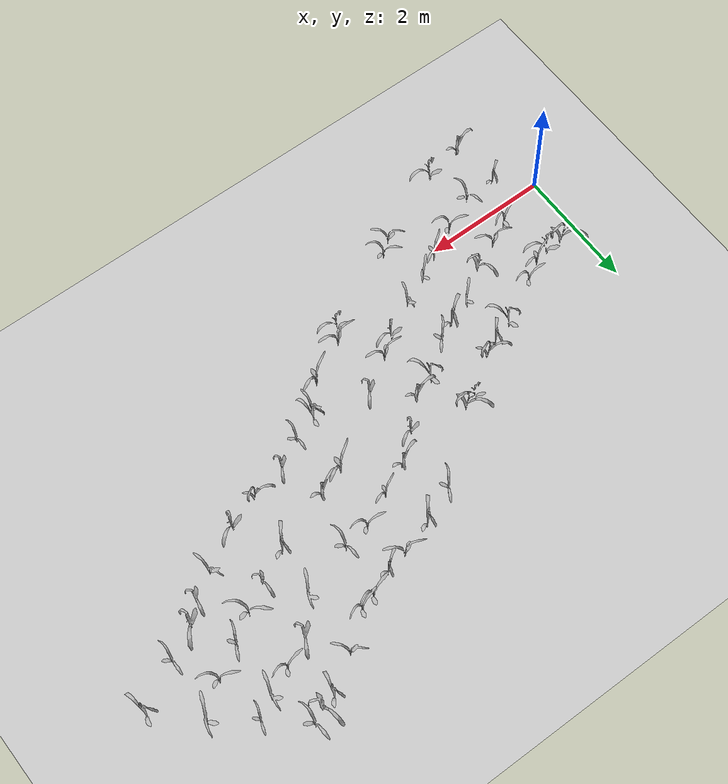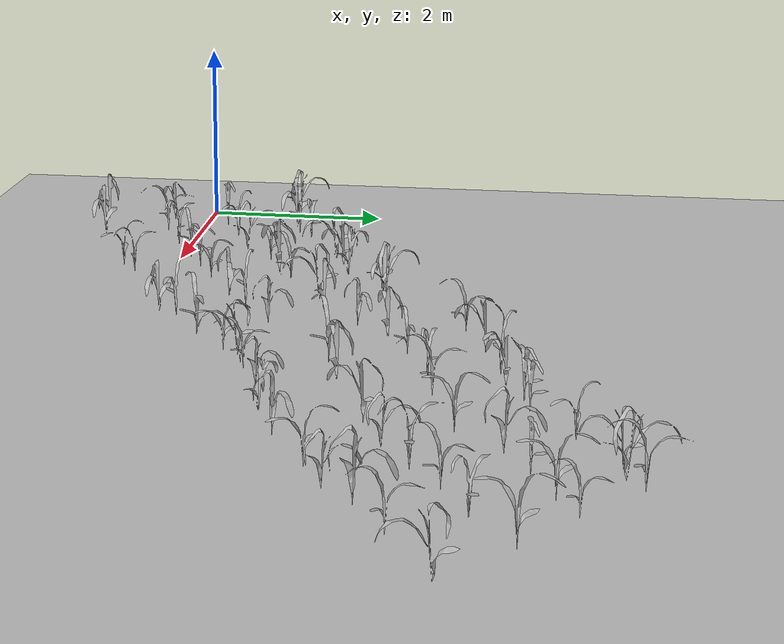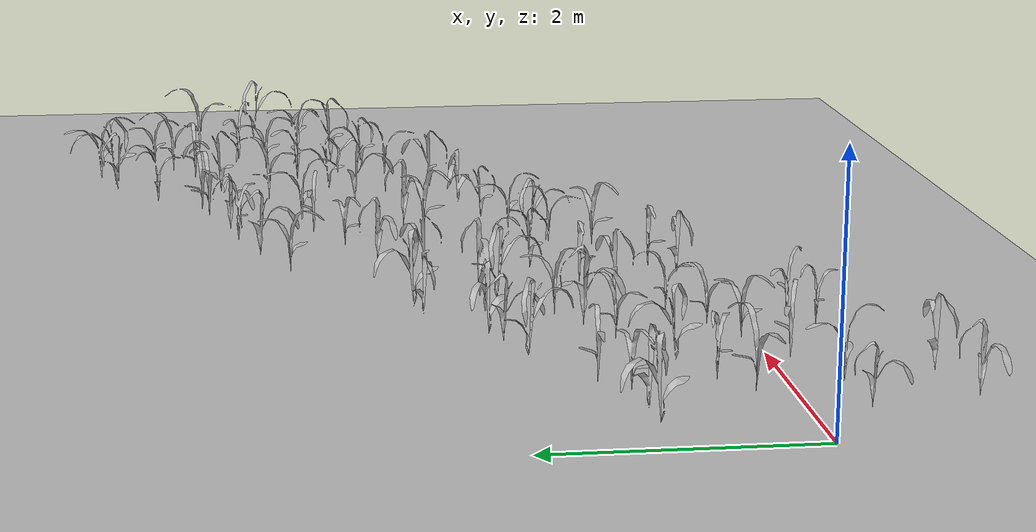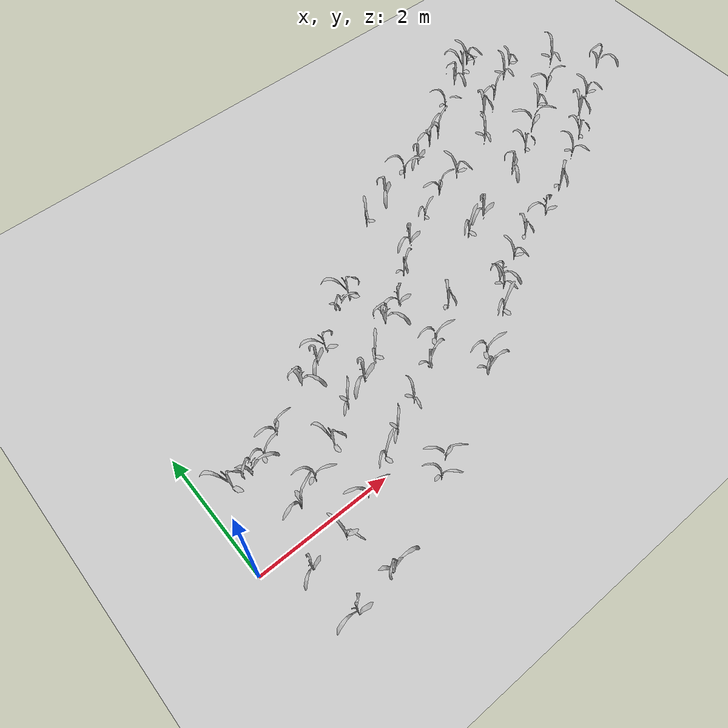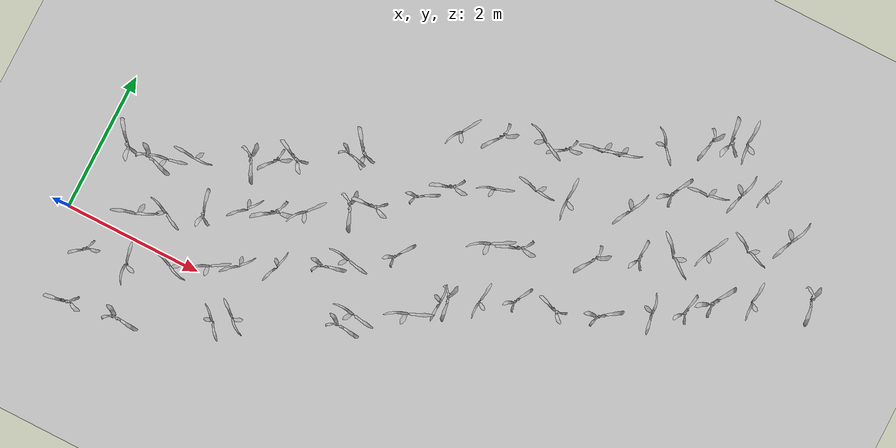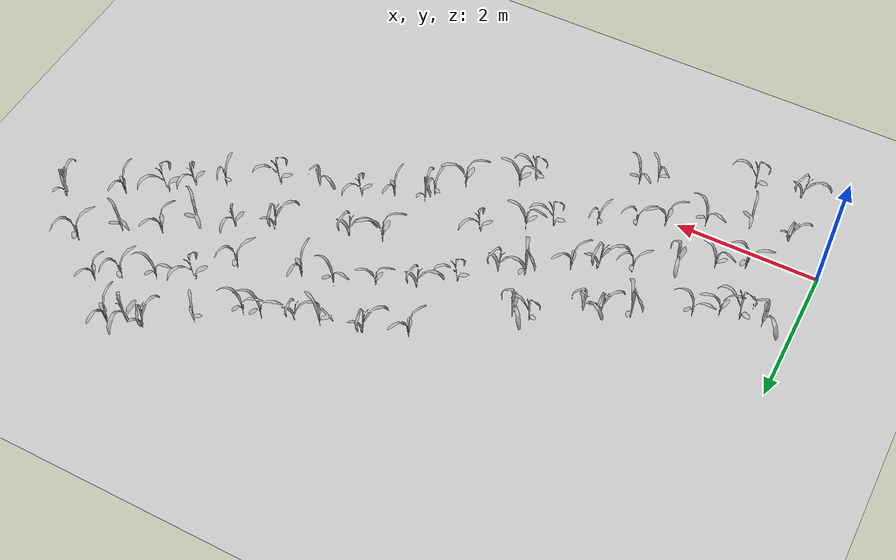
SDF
<sdf version="1.6">
 <world name="default">
  <light name="sun" type="directional">
   <pose>0 0 10 0 -0 0</pose>
   <diffuse>0.8 0.8 0.8 1</diffuse>
   <specular>0.2 0.2 0.2 1</specular>
   <attenuation>
    <range>1000</range>
    <constant>0.9</constant>
    <linear>0.01</linear>
    <quadratic>0.001</quadratic>
   </attenuation>
   <direction>-0.5 0.1 -0.9</direction>
  </light>
  <model name="ground_plane">
   <static>1</static>
   <link name="link">
    <collision name="collision">
     <geometry><plane><normal>0 0 1</normal><size>100 100</size></plane></geometry>
     <surface>
      <contact><collide_bitmask>65535</collide_bitmask></contact>
      <friction><ode><mu>100</mu><mu2>50</mu2></ode></friction>
     </surface>
    </collision>
    <visual name="visual">
     <cast_shadows>0</cast_shadows>
     <geometry><plane><normal>0 0 1</normal><size>100 100</size></plane></geometry>
     <material>
      <script><uri>file://media/materials/scripts/gazebo.material</uri><name>Gazebo/Grey</name></script>
     </material>
    </visual>
   </link>
  </model>
  <gravity>0 0 -9.8</gravity>
  <magnetic_field>6e-06 2.3e-05 -4.2e-05</magnetic_field>
  <atmosphere type="adiabatic"/>
  <physics name="default_physics" default="0" type="ode">
   <max_step_size>0.001</max_step_size>
   <real_time_factor>1</real_time_factor>
   <real_time_update_rate>1000</real_time_update_rate>
  </physics>
  <scene><ambient>0.4 0.4 0.4 1</ambient><background>0.7 0.7 0.7 1</background><shadows>1</shadows></scene>
  <audio><device>default</device></audio>
  <spherical_coordinates>
   <surface_model>EARTH_WGS84</surface_model>
   <latitude_deg>0</latitude_deg>
   <longitude_deg>0</longitude_deg>
   <elevation>0</elevation>
   <heading_deg>0</heading_deg>
  </spherical_coordinates>
  <model name="maize_01_0000">
   <pose>0.3906503861341964 1.0941904161283909 0.05 0 -0 3.0424360916871516</pose>
   <link name="maize_01_0000_link">
    <inertial>
     <mass>5.0</mass>
     <inertia>
      <ixx>0.0033416667</ixx>
      <ixy>0</ixy>
      <ixz>0</ixz>
      <iyy>0.0033416667</iyy>
      <iyz>0</iyz>
      <izz>0.000016666667</izz>
     </inertia>
     <pose>0 0 0.1 0 0 0</pose>
    </inertial>
    <collision name="collision">
     <pose>0 0 0.2 0 -0 0</pose>
     <geometry><box><size>0.02 0.02 0.4</size></box></geometry>
     <surface><friction><ode><mu>10</mu><mu2>10</mu2></ode></friction></surface>
    </collision>
    <visual name="visual">
     <geometry>
      <mesh>
       <uri>model://maize_01/meshes/maize_01.dae</uri>
       <scale>0.67784870440863 0.67784870440863 0.67784870440863</scale>
      </mesh>
     </geometry>
    </visual>
   </link>
  </model>
  <model name="maize_01_0001">
   <pose>0.5515817709031818 -0.390371866211905 0.05 0 -0 4.603411258419125</pose>
   <link name="maize_01_0001_link">
    <inertial>
     <mass>5.0</mass>
     <inertia>
      <ixx>0.0033416667</ixx>
      <ixy>0</ixy>
      <ixz>0</ixz>
      <iyy>0.0033416667</iyy>
      <iyz>0</iyz>
      <izz>0.000016666667</izz>
     </inertia>
     <pose>0 0 0.1 0 0 0</pose>
    </inertial>
    <collision name="collision">
     <pose>0 0 0.2 0 -0 0</pose>
     <geometry><box><size>0.02 0.02 0.4</size></box></geometry>
     <surface><friction><ode><mu>10</mu><mu2>10</mu2></ode></friction></surface>
    </collision>
    <visual name="visual">
     <geometry>
      <mesh>
       <uri>model://maize_01/meshes/maize_01.dae</uri>
       <scale>0.5027295008642508 0.5027295008642508 0.5027295008642508</scale>
      </mesh>
     </geometry>
    </visual>
   </link>
  </model>
  <model name="maize_01_0002">
   <pose>0.6534368972155435 -1.1702270666485124 0.05 0 -0 4.110460014467263</pose>
   <link name="maize_01_0002_link">
    <inertial>
     <mass>5.0</mass>
     <inertia>
      <ixx>0.0033416667</ixx>
      <ixy>0</ixy>
      <ixz>0</ixz>
      <iyy>0.0033416667</iyy>
      <iyz>0</iyz>
      <izz>0.000016666667</izz>
     </inertia>
     <pose>0 0 0.1 0 0 0</pose>
    </inertial>
    <collision name="collision">
     <pose>0 0 0.2 0 -0 0</pose>
     <geometry><box><size>0.02 0.02 0.4</size></box></geometry>
     <surface><friction><ode><mu>10</mu><mu2>10</mu2></ode></friction></surface>
    </collision>
    <visual name="visual">
     <geometry>
      <mesh>
       <uri>model://maize_01/meshes/maize_01.dae</uri>
       <scale>0.6111695617915642 0.6111695617915642 0.6111695617915642</scale>
      </mesh>
     </geometry>
    </visual>
   </link>
  </model>
  <model name="maize_02_0003">
   <pose>0.9037257446686866 0.3282883293863279 0.05 0 -0 5.667359774587816</pose>
   <link name="maize_02_0003_link">
    <inertial>
     <mass>5.0</mass>
     <inertia>
      <ixx>0.0033416667</ixx>
      <ixy>0</ixy>
      <ixz>0</ixz>
      <iyy>0.0033416667</iyy>
      <iyz>0</iyz>
      <izz>0.000016666667</izz>
     </inertia>
     <pose>0 0 0.1 0 0 0</pose>
    </inertial>
    <collision name="collision">
     <pose>0 0 0.2 0 -0 0</pose>
     <geometry><box><size>0.02 0.02 0.4</size></box></geometry>
     <surface><friction><ode><mu>10</mu><mu2>10</mu2></ode></friction></surface>
    </collision>
    <visual name="visual">
     <geometry>
      <mesh>
       <uri>model://maize_02/meshes/maize_02.dae</uri>
       <scale>0.6615052133947399 0.6615052133947399 0.6615052133947399</scale>
      </mesh>
     </geometry>
    </visual>
   </link>
  </model>
  <model name="maize_01_0004">
   <pose>0.6875595545300168 1.1112632524087798 0.05 0 -0 0.4967080085280435</pose>
   <link name="maize_01_0004_link">
    <inertial>
     <mass>5.0</mass>
     <inertia>
      <ixx>0.0033416667</ixx>
      <ixy>0</ixy>
      <ixz>0</ixz>
      <iyy>0.0033416667</iyy>
      <iyz>0</iyz>
      <izz>0.000016666667</izz>
     </inertia>
     <pose>0 0 0.1 0 0 0</pose>
    </inertial>
    <collision name="collision">
     <pose>0 0 0.2 0 -0 0</pose>
     <geometry><box><size>0.02 0.02 0.4</size></box></geometry>
     <surface><friction><ode><mu>10</mu><mu2>10</mu2></ode></friction></surface>
    </collision>
    <visual name="visual">
     <geometry>
      <mesh>
       <uri>model://maize_01/meshes/maize_01.dae</uri>
       <scale>0.6530112409743611 0.6530112409743611 0.6530112409743611</scale>
      </mesh>
     </geometry>
    </visual>
   </link>
  </model>
  <model name="maize_02_0005">
   <pose>1.1053254814833162 -0.34731469430018386 0.05 0 -0 3.9474850268500807</pose>
   <link name="maize_02_0005_link">
    <inertial>
     <mass>5.0</mass>
     <inertia>
      <ixx>0.0033416667</ixx>
      <ixy>0</ixy>
      <ixz>0</ixz>
      <iyy>0.0033416667</iyy>
      <iyz>0</iyz>
      <izz>0.000016666667</izz>
     </inertia>
     <pose>0 0 0.1 0 0 0</pose>
    </inertial>
    <collision name="collision">
     <pose>0 0 0.2 0 -0 0</pose>
     <geometry><box><size>0.02 0.02 0.4</size></box></geometry>
     <surface><friction><ode><mu>10</mu><mu2>10</mu2></ode></friction></surface>
    </collision>
    <visual name="visual">
     <geometry>
      <mesh>
       <uri>model://maize_02/meshes/maize_02.dae</uri>
       <scale>0.6000571639713058 0.6000571639713058 0.6000571639713058</scale>
      </mesh>
     </geometry>
    </visual>
   </link>
  </model>
  <model name="maize_01_0006">
   <pose>1.281661355598756 -1.0561770014182132 0.05 0 -0 0.7080012229232223</pose>
   <link name="maize_01_0006_link">
    <inertial>
     <mass>5.0</mass>
     <inertia>
      <ixx>0.0033416667</ixx>
      <ixy>0</ixy>
      <ixz>0</ixz>
      <iyy>0.0033416667</iyy>
      <iyz>0</iyz>
      <izz>0.000016666667</izz>
     </inertia>
     <pose>0 0 0.1 0 0 0</pose>
    </inertial>
    <collision name="collision">
     <pose>0 0 0.2 0 -0 0</pose>
     <geometry><box><size>0.02 0.02 0.4</size></box></geometry>
     <surface><friction><ode><mu>10</mu><mu2>10</mu2></ode></friction></surface>
    </collision>
    <visual name="visual">
     <geometry>
      <mesh>
       <uri>model://maize_01/meshes/maize_01.dae</uri>
       <scale>0.6288869688617147 0.6288869688617147 0.6288869688617147</scale>
      </mesh>
     </geometry>
    </visual>
   </link>
  </model>
  <model name="maize_02_0007">
   <pose>1.2696388292588123 0.5186154928203635 0.05 0 -0 1.7338231067781802</pose>
   <link name="maize_02_0007_link">
    <inertial>
     <mass>5.0</mass>
     <inertia>
      <ixx>0.0033416667</ixx>
      <ixy>0</ixy>
      <ixz>0</ixz>
      <iyy>0.0033416667</iyy>
      <iyz>0</iyz>
      <izz>0.000016666667</izz>
     </inertia>
     <pose>0 0 0.1 0 0 0</pose>
    </inertial>
    <collision name="collision">
     <pose>0 0 0.2 0 -0 0</pose>
     <geometry><box><size>0.02 0.02 0.4</size></box></geometry>
     <surface><friction><ode><mu>10</mu><mu2>10</mu2></ode></friction></surface>
    </collision>
    <visual name="visual">
     <geometry>
      <mesh>
       <uri>model://maize_02/meshes/maize_02.dae</uri>
       <scale>0.5775966646368987 0.5775966646368987 0.5775966646368987</scale>
      </mesh>
     </geometry>
    </visual>
   </link>
  </model>
  <model name="maize_02_0008">
   <pose>0.9436205945427015 1.1843774074831916 0.05 0 -0 2.4081954604851514</pose>
   <link name="maize_02_0008_link">
    <inertial>
     <mass>5.0</mass>
     <inertia>
      <ixx>0.0033416667</ixx>
      <ixy>0</ixy>
      <ixz>0</ixz>
      <iyy>0.0033416667</iyy>
      <iyz>0</iyz>
      <izz>0.000016666667</izz>
     </inertia>
     <pose>0 0 0.1 0 0 0</pose>
    </inertial>
    <collision name="collision">
     <pose>0 0 0.2 0 -0 0</pose>
     <geometry><box><size>0.02 0.02 0.4</size></box></geometry>
     <surface><friction><ode><mu>10</mu><mu2>10</mu2></ode></friction></surface>
    </collision>
    <visual name="visual">
     <geometry>
      <mesh>
       <uri>model://maize_02/meshes/maize_02.dae</uri>
       <scale>0.5699472859153585 0.5699472859153585 0.5699472859153585</scale>
      </mesh>
     </geometry>
    </visual>
   </link>
  </model>
  <model name="maize_02_0009">
   <pose>1.6473226780658463 -0.09655022891856302 0.05 0 -0 4.94809720174679</pose>
   <link name="maize_02_0009_link">
    <inertial>
     <mass>5.0</mass>
     <inertia>
      <ixx>0.0033416667</ixx>
      <ixy>0</ixy>
      <ixz>0</ixz>
      <iyy>0.0033416667</iyy>
      <iyz>0</iyz>
      <izz>0.000016666667</izz>
     </inertia>
     <pose>0 0 0.1 0 0 0</pose>
    </inertial>
    <collision name="collision">
     <pose>0 0 0.2 0 -0 0</pose>
     <geometry><box><size>0.02 0.02 0.4</size></box></geometry>
     <surface><friction><ode><mu>10</mu><mu2>10</mu2></ode></friction></surface>
    </collision>
    <visual name="visual">
     <geometry>
      <mesh>
       <uri>model://maize_02/meshes/maize_02.dae</uri>
       <scale>0.6046377324987864 0.6046377324987864 0.6046377324987864</scale>
      </mesh>
     </geometry>
    </visual>
   </link>
  </model>
  <model name="maize_01_0010">
   <pose>1.7393277898649264 0.7210873634953373 0.05 0 -0 2.614993399987889</pose>
   <link name="maize_01_0010_link">
    <inertial>
     <mass>5.0</mass>
     <inertia>
      <ixx>0.0033416667</ixx>
      <ixy>0</ixy>
      <ixz>0</ixz>
      <iyy>0.0033416667</iyy>
      <iyz>0</iyz>
      <izz>0.000016666667</izz>
     </inertia>
     <pose>0 0 0.1 0 0 0</pose>
    </inertial>
    <collision name="collision">
     <pose>0 0 0.2 0 -0 0</pose>
     <geometry><box><size>0.02 0.02 0.4</size></box></geometry>
     <surface><friction><ode><mu>10</mu><mu2>10</mu2></ode></friction></surface>
    </collision>
    <visual name="visual">
     <geometry>
      <mesh>
       <uri>model://maize_01/meshes/maize_01.dae</uri>
       <scale>0.6220417443570617 0.6220417443570617 0.6220417443570617</scale>
      </mesh>
     </geometry>
    </visual>
   </link>
  </model>
  <model name="maize_02_0011">
   <pose>1.2544440834057946 1.3702231027017293 0.05 0 -0 5.288871814829883</pose>
   <link name="maize_02_0011_link">
    <inertial>
     <mass>5.0</mass>
     <inertia>
      <ixx>0.0033416667</ixx>
      <ixy>0</ixy>
      <ixz>0</ixz>
      <iyy>0.0033416667</iyy>
      <iyz>0</iyz>
      <izz>0.000016666667</izz>
     </inertia>
     <pose>0 0 0.1 0 0 0</pose>
    </inertial>
    <collision name="collision">
     <pose>0 0 0.2 0 -0 0</pose>
     <geometry><box><size>0.02 0.02 0.4</size></box></geometry>
     <surface><friction><ode><mu>10</mu><mu2>10</mu2></ode></friction></surface>
    </collision>
    <visual name="visual">
     <geometry>
      <mesh>
       <uri>model://maize_02/meshes/maize_02.dae</uri>
       <scale>0.5764412475349001 0.5764412475349001 0.5764412475349001</scale>
      </mesh>
     </geometry>
    </visual>
   </link>
  </model>
  <model name="maize_02_0012">
   <pose>2.1356804657078694 0.14822536734168001 0.05 0 -0 2.737955239679464</pose>
   <link name="maize_02_0012_link">
    <inertial>
     <mass>5.0</mass>
     <inertia>
      <ixx>0.0033416667</ixx>
      <ixy>0</ixy>
      <ixz>0</ixz>
      <iyy>0.0033416667</iyy>
      <iyz>0</iyz>
      <izz>0.000016666667</izz>
     </inertia>
     <pose>0 0 0.1 0 0 0</pose>
    </inertial>
    <collision name="collision">
     <pose>0 0 0.2 0 -0 0</pose>
     <geometry><box><size>0.02 0.02 0.4</size></box></geometry>
     <surface><friction><ode><mu>10</mu><mu2>10</mu2></ode></friction></surface>
    </collision>
    <visual name="visual">
     <geometry>
      <mesh>
       <uri>model://maize_02/meshes/maize_02.dae</uri>
       <scale>0.5850642795302832 0.5850642795302832 0.5850642795302832</scale>
      </mesh>
     </geometry>
    </visual>
   </link>
  </model>
  <model name="maize_02_0013">
   <pose>2.521593429491164 -0.516472683149832 0.05 0 -0 1.3347260085552122</pose>
   <link name="maize_02_0013_link">
    <inertial>
     <mass>5.0</mass>
     <inertia>
      <ixx>0.0033416667</ixx>
      <ixy>0</ixy>
      <ixz>0</ixz>
      <iyy>0.0033416667</iyy>
      <iyz>0</iyz>
      <izz>0.000016666667</izz>
     </inertia>
     <pose>0 0 0.1 0 0 0</pose>
    </inertial>
    <collision name="collision">
     <pose>0 0 0.2 0 -0 0</pose>
     <geometry><box><size>0.02 0.02 0.4</size></box></geometry>
     <surface><friction><ode><mu>10</mu><mu2>10</mu2></ode></friction></surface>
    </collision>
    <visual name="visual">
     <geometry>
      <mesh>
       <uri>model://maize_02/meshes/maize_02.dae</uri>
       <scale>0.5275001462943436 0.5275001462943436 0.5275001462943436</scale>
      </mesh>
     </geometry>
    </visual>
   </link>
  </model>
  <model name="maize_02_0014">
   <pose>2.2281992092598872 1.070648200209497 0.05 0 -0 6.131660546720616</pose>
   <link name="maize_02_0014_link">
    <inertial>
     <mass>5.0</mass>
     <inertia>
      <ixx>0.0033416667</ixx>
      <ixy>0</ixy>
      <ixz>0</ixz>
      <iyy>0.0033416667</iyy>
      <iyz>0</iyz>
      <izz>0.000016666667</izz>
     </inertia>
     <pose>0 0 0.1 0 0 0</pose>
    </inertial>
    <collision name="collision">
     <pose>0 0 0.2 0 -0 0</pose>
     <geometry><box><size>0.02 0.02 0.4</size></box></geometry>
     <surface><friction><ode><mu>10</mu><mu2>10</mu2></ode></friction></surface>
    </collision>
    <visual name="visual">
     <geometry>
      <mesh>
       <uri>model://maize_02/meshes/maize_02.dae</uri>
       <scale>0.5508786357015456 0.5508786357015456 0.5508786357015456</scale>
      </mesh>
     </geometry>
    </visual>
   </link>
  </model>
  <model name="maize_01_0015">
   <pose>1.949516926842686 1.7543932494482717 0.05 0 -0 5.975872709018149</pose>
   <link name="maize_01_0015_link">
    <inertial>
     <mass>5.0</mass>
     <inertia>
      <ixx>0.0033416667</ixx>
      <ixy>0</ixy>
      <ixz>0</ixz>
      <iyy>0.0033416667</iyy>
      <iyz>0</iyz>
      <izz>0.000016666667</izz>
     </inertia>
     <pose>0 0 0.1 0 0 0</pose>
    </inertial>
    <collision name="collision">
     <pose>0 0 0.2 0 -0 0</pose>
     <geometry><box><size>0.02 0.02 0.4</size></box></geometry>
     <surface><friction><ode><mu>10</mu><mu2>10</mu2></ode></friction></surface>
    </collision>
    <visual name="visual">
     <geometry>
      <mesh>
       <uri>model://maize_01/meshes/maize_01.dae</uri>
       <scale>0.6465259724280888 0.6465259724280888 0.6465259724280888</scale>
      </mesh>
     </geometry>
    </visual>
   </link>
  </model>
  <model name="maize_02_0016">
   <pose>2.4890503552776284 0.33247659587417167 0.05 0 -0 6.093076066105277</pose>
   <link name="maize_02_0016_link">
    <inertial>
     <mass>5.0</mass>
     <inertia>
      <ixx>0.0033416667</ixx>
      <ixy>0</ixy>
      <ixz>0</ixz>
      <iyy>0.0033416667</iyy>
      <iyz>0</iyz>
      <izz>0.000016666667</izz>
     </inertia>
     <pose>0 0 0.1 0 0 0</pose>
    </inertial>
    <collision name="collision">
     <pose>0 0 0.2 0 -0 0</pose>
     <geometry><box><size>0.02 0.02 0.4</size></box></geometry>
     <surface><friction><ode><mu>10</mu><mu2>10</mu2></ode></friction></surface>
    </collision>
    <visual name="visual">
     <geometry>
      <mesh>
       <uri>model://maize_02/meshes/maize_02.dae</uri>
       <scale>0.5315655074172222 0.5315655074172222 0.5315655074172222</scale>
      </mesh>
     </geometry>
    </visual>
   </link>
  </model>
  <model name="maize_02_0017">
   <pose>2.7375041220000815 -0.3422672742953123 0.05 0 -0 4.6291913747215325</pose>
   <link name="maize_02_0017_link">
    <inertial>
     <mass>5.0</mass>
     <inertia>
      <ixx>0.0033416667</ixx>
      <ixy>0</ixy>
      <ixz>0</ixz>
      <iyy>0.0033416667</iyy>
      <iyz>0</iyz>
      <izz>0.000016666667</izz>
     </inertia>
     <pose>0 0 0.1 0 0 0</pose>
    </inertial>
    <collision name="collision">
     <pose>0 0 0.2 0 -0 0</pose>
     <geometry><box><size>0.02 0.02 0.4</size></box></geometry>
     <surface><friction><ode><mu>10</mu><mu2>10</mu2></ode></friction></surface>
    </collision>
    <visual name="visual">
     <geometry>
      <mesh>
       <uri>model://maize_02/meshes/maize_02.dae</uri>
       <scale>0.5603229692819149 0.5603229692819149 0.5603229692819149</scale>
      </mesh>
     </geometry>
    </visual>
   </link>
  </model>
  <model name="maize_01_0018">
   <pose>2.651156521702104 1.2415051627822342 0.05 0 -0 4.555210356887598</pose>
   <link name="maize_01_0018_link">
    <inertial>
     <mass>5.0</mass>
     <inertia>
      <ixx>0.0033416667</ixx>
      <ixy>0</ixy>
      <ixz>0</ixz>
      <iyy>0.0033416667</iyy>
      <iyz>0</iyz>
      <izz>0.000016666667</izz>
     </inertia>
     <pose>0 0 0.1 0 0 0</pose>
    </inertial>
    <collision name="collision">
     <pose>0 0 0.2 0 -0 0</pose>
     <geometry><box><size>0.02 0.02 0.4</size></box></geometry>
     <surface><friction><ode><mu>10</mu><mu2>10</mu2></ode></friction></surface>
    </collision>
    <visual name="visual">
     <geometry>
      <mesh>
       <uri>model://maize_01/meshes/maize_01.dae</uri>
       <scale>0.6811169366257742 0.6811169366257742 0.6811169366257742</scale>
      </mesh>
     </geometry>
    </visual>
   </link>
  </model>
  <model name="maize_01_0019">
   <pose>2.322023597308829 1.8909239201625239 0.05 0 -0 4.808320298732225</pose>
   <link name="maize_01_0019_link">
    <inertial>
     <mass>5.0</mass>
     <inertia>
      <ixx>0.0033416667</ixx>
      <ixy>0</ixy>
      <ixz>0</ixz>
      <iyy>0.0033416667</iyy>
      <iyz>0</iyz>
      <izz>0.000016666667</izz>
     </inertia>
     <pose>0 0 0.1 0 0 0</pose>
    </inertial>
    <collision name="collision">
     <pose>0 0 0.2 0 -0 0</pose>
     <geometry><box><size>0.02 0.02 0.4</size></box></geometry>
     <surface><friction><ode><mu>10</mu><mu2>10</mu2></ode></friction></surface>
    </collision>
    <visual name="visual">
     <geometry>
      <mesh>
       <uri>model://maize_01/meshes/maize_01.dae</uri>
       <scale>0.5655274052204861 0.5655274052204861 0.5655274052204861</scale>
      </mesh>
     </geometry>
    </visual>
   </link>
  </model>
  <model name="maize_02_0020">
   <pose>2.9599004914560223 0.5525120589761708 0.05 0 -0 0.28839328746539966</pose>
   <link name="maize_02_0020_link">
    <inertial>
     <mass>5.0</mass>
     <inertia>
      <ixx>0.0033416667</ixx>
      <ixy>0</ixy>
      <ixz>0</ixz>
      <iyy>0.0033416667</iyy>
      <iyz>0</iyz>
      <izz>0.000016666667</izz>
     </inertia>
     <pose>0 0 0.1 0 0 0</pose>
    </inertial>
    <collision name="collision">
     <pose>0 0 0.2 0 -0 0</pose>
     <geometry><box><size>0.02 0.02 0.4</size></box></geometry>
     <surface><friction><ode><mu>10</mu><mu2>10</mu2></ode></friction></surface>
    </collision>
    <visual name="visual">
     <geometry>
      <mesh>
       <uri>model://maize_02/meshes/maize_02.dae</uri>
       <scale>0.5145858625740877 0.5145858625740877 0.5145858625740877</scale>
      </mesh>
     </geometry>
    </visual>
   </link>
  </model>
  <model name="maize_02_0021">
   <pose>2.9718184976784623 1.4130837722674536 0.05 0 -0 3.0545142510817858</pose>
   <link name="maize_02_0021_link">
    <inertial>
     <mass>5.0</mass>
     <inertia>
      <ixx>0.0033416667</ixx>
      <ixy>0</ixy>
      <ixz>0</ixz>
      <iyy>0.0033416667</iyy>
      <iyz>0</iyz>
      <izz>0.000016666667</izz>
     </inertia>
     <pose>0 0 0.1 0 0 0</pose>
    </inertial>
    <collision name="collision">
     <pose>0 0 0.2 0 -0 0</pose>
     <geometry><box><size>0.02 0.02 0.4</size></box></geometry>
     <surface><friction><ode><mu>10</mu><mu2>10</mu2></ode></friction></surface>
    </collision>
    <visual name="visual">
     <geometry>
      <mesh>
       <uri>model://maize_02/meshes/maize_02.dae</uri>
       <scale>0.5996508771102989 0.5996508771102989 0.5996508771102989</scale>
      </mesh>
     </geometry>
    </visual>
   </link>
  </model>
  <model name="maize_01_0022">
   <pose>2.542234352776703 1.9741148003283353 0.05 0 -0 3.4628253279191092</pose>
   <link name="maize_01_0022_link">
    <inertial>
     <mass>5.0</mass>
     <inertia>
      <ixx>0.0033416667</ixx>
      <ixy>0</ixy>
      <ixz>0</ixz>
      <iyy>0.0033416667</iyy>
      <iyz>0</iyz>
      <izz>0.000016666667</izz>
     </inertia>
     <pose>0 0 0.1 0 0 0</pose>
    </inertial>
    <collision name="collision">
     <pose>0 0 0.2 0 -0 0</pose>
     <geometry><box><size>0.02 0.02 0.4</size></box></geometry>
     <surface><friction><ode><mu>10</mu><mu2>10</mu2></ode></friction></surface>
    </collision>
    <visual name="visual">
     <geometry>
      <mesh>
       <uri>model://maize_01/meshes/maize_01.dae</uri>
       <scale>0.6061441355189363 0.6061441355189363 0.6061441355189363</scale>
      </mesh>
     </geometry>
    </visual>
   </link>
  </model>
  <model name="maize_01_0023">
   <pose>3.489873220159218 0.8493553534492073 0.05 0 -0 1.0358009869210594</pose>
   <link name="maize_01_0023_link">
    <inertial>
     <mass>5.0</mass>
     <inertia>
      <ixx>0.0033416667</ixx>
      <ixy>0</ixy>
      <ixz>0</ixz>
      <iyy>0.0033416667</iyy>
      <iyz>0</iyz>
      <izz>0.000016666667</izz>
     </inertia>
     <pose>0 0 0.1 0 0 0</pose>
    </inertial>
    <collision name="collision">
     <pose>0 0 0.2 0 -0 0</pose>
     <geometry><box><size>0.02 0.02 0.4</size></box></geometry>
     <surface><friction><ode><mu>10</mu><mu2>10</mu2></ode></friction></surface>
    </collision>
    <visual name="visual">
     <geometry>
      <mesh>
       <uri>model://maize_01/meshes/maize_01.dae</uri>
       <scale>0.584020593496818 0.584020593496818 0.584020593496818</scale>
      </mesh>
     </geometry>
    </visual>
   </link>
  </model>
  <model name="maize_01_0024">
   <pose>4.047379828273896 0.23922231375552877 0.05 0 -0 0.6851542206814848</pose>
   <link name="maize_01_0024_link">
    <inertial>
     <mass>5.0</mass>
     <inertia>
      <ixx>0.0033416667</ixx>
      <ixy>0</ixy>
      <ixz>0</ixz>
      <iyy>0.0033416667</iyy>
      <iyz>0</iyz>
      <izz>0.000016666667</izz>
     </inertia>
     <pose>0 0 0.1 0 0 0</pose>
    </inertial>
    <collision name="collision">
     <pose>0 0 0.2 0 -0 0</pose>
     <geometry><box><size>0.02 0.02 0.4</size></box></geometry>
     <surface><friction><ode><mu>10</mu><mu2>10</mu2></ode></friction></surface>
    </collision>
    <visual name="visual">
     <geometry>
      <mesh>
       <uri>model://maize_01/meshes/maize_01.dae</uri>
       <scale>0.5800443365220155 0.5800443365220155 0.5800443365220155</scale>
      </mesh>
     </geometry>
    </visual>
   </link>
  </model>
  <model name="maize_01_0025">
   <pose>3.462279687654834 1.7900703254089694 0.05 0 -0 5.905350689487405</pose>
   <link name="maize_01_0025_link">
    <inertial>
     <mass>5.0</mass>
     <inertia>
      <ixx>0.0033416667</ixx>
      <ixy>0</ixy>
      <ixz>0</ixz>
      <iyy>0.0033416667</iyy>
      <iyz>0</iyz>
      <izz>0.000016666667</izz>
     </inertia>
     <pose>0 0 0.1 0 0 0</pose>
    </inertial>
    <collision name="collision">
     <pose>0 0 0.2 0 -0 0</pose>
     <geometry><box><size>0.02 0.02 0.4</size></box></geometry>
     <surface><friction><ode><mu>10</mu><mu2>10</mu2></ode></friction></surface>
    </collision>
    <visual name="visual">
     <geometry>
      <mesh>
       <uri>model://maize_01/meshes/maize_01.dae</uri>
       <scale>0.658068712293799 0.658068712293799 0.658068712293799</scale>
      </mesh>
     </geometry>
    </visual>
   </link>
  </model>
  <model name="maize_01_0026">
   <pose>3.10780085140256 2.402169679909919 0.05 0 -0 0.5519448590636261</pose>
   <link name="maize_01_0026_link">
    <inertial>
     <mass>5.0</mass>
     <inertia>
      <ixx>0.0033416667</ixx>
      <ixy>0</ixy>
      <ixz>0</ixz>
      <iyy>0.0033416667</iyy>
      <iyz>0</iyz>
      <izz>0.000016666667</izz>
     </inertia>
     <pose>0 0 0.1 0 0 0</pose>
    </inertial>
    <collision name="collision">
     <pose>0 0 0.2 0 -0 0</pose>
     <geometry><box><size>0.02 0.02 0.4</size></box></geometry>
     <surface><friction><ode><mu>10</mu><mu2>10</mu2></ode></friction></surface>
    </collision>
    <visual name="visual">
     <geometry>
      <mesh>
       <uri>model://maize_01/meshes/maize_01.dae</uri>
       <scale>0.5024001148821585 0.5024001148821585 0.5024001148821585</scale>
      </mesh>
     </geometry>
    </visual>
   </link>
  </model>
  <model name="maize_02_0027">
   <pose>3.8012030082236548 1.0842681720826082 0.05 0 -0 2.0147098821106777</pose>
   <link name="maize_02_0027_link">
    <inertial>
     <mass>5.0</mass>
     <inertia>
      <ixx>0.0033416667</ixx>
      <ixy>0</ixy>
      <ixz>0</ixz>
      <iyy>0.0033416667</iyy>
      <iyz>0</iyz>
      <izz>0.000016666667</izz>
     </inertia>
     <pose>0 0 0.1 0 0 0</pose>
    </inertial>
    <collision name="collision">
     <pose>0 0 0.2 0 -0 0</pose>
     <geometry><box><size>0.02 0.02 0.4</size></box></geometry>
     <surface><friction><ode><mu>10</mu><mu2>10</mu2></ode></friction></surface>
    </collision>
    <visual name="visual">
     <geometry>
      <mesh>
       <uri>model://maize_02/meshes/maize_02.dae</uri>
       <scale>0.6093589843163167 0.6093589843163167 0.6093589843163167</scale>
      </mesh>
     </geometry>
    </visual>
   </link>
  </model>
  <model name="maize_02_0028">
   <pose>4.19968755216005 0.452078163699329 0.05 0 -0 2.0565473337517535</pose>
   <link name="maize_02_0028_link">
    <inertial>
     <mass>5.0</mass>
     <inertia>
      <ixx>0.0033416667</ixx>
      <ixy>0</ixy>
      <ixz>0</ixz>
      <iyy>0.0033416667</iyy>
      <iyz>0</iyz>
      <izz>0.000016666667</izz>
     </inertia>
     <pose>0 0 0.1 0 0 0</pose>
    </inertial>
    <collision name="collision">
     <pose>0 0 0.2 0 -0 0</pose>
     <geometry><box><size>0.02 0.02 0.4</size></box></geometry>
     <surface><friction><ode><mu>10</mu><mu2>10</mu2></ode></friction></surface>
    </collision>
    <visual name="visual">
     <geometry>
      <mesh>
       <uri>model://maize_02/meshes/maize_02.dae</uri>
       <scale>0.6253034927847808 0.6253034927847808 0.6253034927847808</scale>
      </mesh>
     </geometry>
    </visual>
   </link>
  </model>
  <model name="maize_01_0029">
   <pose>3.81432318541326 1.8985593585177398 0.05 0 -0 4.020082010859396</pose>
   <link name="maize_01_0029_link">
    <inertial>
     <mass>5.0</mass>
     <inertia>
      <ixx>0.0033416667</ixx>
      <ixy>0</ixy>
      <ixz>0</ixz>
      <iyy>0.0033416667</iyy>
      <iyz>0</iyz>
      <izz>0.000016666667</izz>
     </inertia>
     <pose>0 0 0.1 0 0 0</pose>
    </inertial>
    <collision name="collision">
     <pose>0 0 0.2 0 -0 0</pose>
     <geometry><box><size>0.02 0.02 0.4</size></box></geometry>
     <surface><friction><ode><mu>10</mu><mu2>10</mu2></ode></friction></surface>
    </collision>
    <visual name="visual">
     <geometry>
      <mesh>
       <uri>model://maize_01/meshes/maize_01.dae</uri>
       <scale>0.613975244292793 0.613975244292793 0.613975244292793</scale>
      </mesh>
     </geometry>
    </visual>
   </link>
  </model>
  <model name="maize_01_0030">
   <pose>3.331339709816383 2.4620784243587166 0.05 0 -0 3.0100959707617725</pose>
   <link name="maize_01_0030_link">
    <inertial>
     <mass>5.0</mass>
     <inertia>
      <ixx>0.0033416667</ixx>
      <ixy>0</ixy>
      <ixz>0</ixz>
      <iyy>0.0033416667</iyy>
      <iyz>0</iyz>
      <izz>0.000016666667</izz>
     </inertia>
     <pose>0 0 0.1 0 0 0</pose>
    </inertial>
    <collision name="collision">
     <pose>0 0 0.2 0 -0 0</pose>
     <geometry><box><size>0.02 0.02 0.4</size></box></geometry>
     <surface><friction><ode><mu>10</mu><mu2>10</mu2></ode></friction></surface>
    </collision>
    <visual name="visual">
     <geometry>
      <mesh>
       <uri>model://maize_01/meshes/maize_01.dae</uri>
       <scale>0.6720729560431616 0.6720729560431616 0.6720729560431616</scale>
      </mesh>
     </geometry>
    </visual>
   </link>
  </model>
  <model name="maize_01_0031">
   <pose>4.332515377387643 1.4098711547283245 0.05 0 -0 1.757153079909286</pose>
   <link name="maize_01_0031_link">
    <inertial>
     <mass>5.0</mass>
     <inertia>
      <ixx>0.0033416667</ixx>
      <ixy>0</ixy>
      <ixz>0</ixz>
      <iyy>0.0033416667</iyy>
      <iyz>0</iyz>
      <izz>0.000016666667</izz>
     </inertia>
     <pose>0 0 0.1 0 0 0</pose>
    </inertial>
    <collision name="collision">
     <pose>0 0 0.2 0 -0 0</pose>
     <geometry><box><size>0.02 0.02 0.4</size></box></geometry>
     <surface><friction><ode><mu>10</mu><mu2>10</mu2></ode></friction></surface>
    </collision>
    <visual name="visual">
     <geometry>
      <mesh>
       <uri>model://maize_01/meshes/maize_01.dae</uri>
       <scale>0.5573014963681552 0.5573014963681552 0.5573014963681552</scale>
      </mesh>
     </geometry>
    </visual>
   </link>
  </model>
  <model name="maize_02_0032">
   <pose>4.859590877642029 0.8064933506026067 0.05 0 -0 2.5973756348950037</pose>
   <link name="maize_02_0032_link">
    <inertial>
     <mass>5.0</mass>
     <inertia>
      <ixx>0.0033416667</ixx>
      <ixy>0</ixy>
      <ixz>0</ixz>
      <iyy>0.0033416667</iyy>
      <iyz>0</iyz>
      <izz>0.000016666667</izz>
     </inertia>
     <pose>0 0 0.1 0 0 0</pose>
    </inertial>
    <collision name="collision">
     <pose>0 0 0.2 0 -0 0</pose>
     <geometry><box><size>0.02 0.02 0.4</size></box></geometry>
     <surface><friction><ode><mu>10</mu><mu2>10</mu2></ode></friction></surface>
    </collision>
    <visual name="visual">
     <geometry>
      <mesh>
       <uri>model://maize_02/meshes/maize_02.dae</uri>
       <scale>0.6738526575826701 0.6738526575826701 0.6738526575826701</scale>
      </mesh>
     </geometry>
    </visual>
   </link>
  </model>
  <model name="maize_01_0033">
   <pose>4.225841059403212 2.288848529619568 0.05 0 -0 1.3169442561918367</pose>
   <link name="maize_01_0033_link">
    <inertial>
     <mass>5.0</mass>
     <inertia>
      <ixx>0.0033416667</ixx>
      <ixy>0</ixy>
      <ixz>0</ixz>
      <iyy>0.0033416667</iyy>
      <iyz>0</iyz>
      <izz>0.000016666667</izz>
     </inertia>
     <pose>0 0 0.1 0 0 0</pose>
    </inertial>
    <collision name="collision">
     <pose>0 0 0.2 0 -0 0</pose>
     <geometry><box><size>0.02 0.02 0.4</size></box></geometry>
     <surface><friction><ode><mu>10</mu><mu2>10</mu2></ode></friction></surface>
    </collision>
    <visual name="visual">
     <geometry>
      <mesh>
       <uri>model://maize_01/meshes/maize_01.dae</uri>
       <scale>0.5379990391688103 0.5379990391688103 0.5379990391688103</scale>
      </mesh>
     </geometry>
    </visual>
   </link>
  </model>
  <model name="maize_02_0034">
   <pose>5.173450004030893 1.1315763102588983 0.05 0 -0 0.6013101745679047</pose>
   <link name="maize_02_0034_link">
    <inertial>
     <mass>5.0</mass>
     <inertia>
      <ixx>0.0033416667</ixx>
      <ixy>0</ixy>
      <ixz>0</ixz>
      <iyy>0.0033416667</iyy>
      <iyz>0</iyz>
      <izz>0.000016666667</izz>
     </inertia>
     <pose>0 0 0.1 0 0 0</pose>
    </inertial>
    <collision name="collision">
     <pose>0 0 0.2 0 -0 0</pose>
     <geometry><box><size>0.02 0.02 0.4</size></box></geometry>
     <surface><friction><ode><mu>10</mu><mu2>10</mu2></ode></friction></surface>
    </collision>
    <visual name="visual">
     <geometry>
      <mesh>
       <uri>model://maize_02/meshes/maize_02.dae</uri>
       <scale>0.5357407810014682 0.5357407810014682 0.5357407810014682</scale>
      </mesh>
     </geometry>
    </visual>
   </link>
  </model>
  <model name="maize_01_0035">
   <pose>4.648873566130375 2.642791740752094 0.05 0 -0 4.281673387435433</pose>
   <link name="maize_01_0035_link">
    <inertial>
     <mass>5.0</mass>
     <inertia>
      <ixx>0.0033416667</ixx>
      <ixy>0</ixy>
      <ixz>0</ixz>
      <iyy>0.0033416667</iyy>
      <iyz>0</iyz>
      <izz>0.000016666667</izz>
     </inertia>
     <pose>0 0 0.1 0 0 0</pose>
    </inertial>
    <collision name="collision">
     <pose>0 0 0.2 0 -0 0</pose>
     <geometry><box><size>0.02 0.02 0.4</size></box></geometry>
     <surface><friction><ode><mu>10</mu><mu2>10</mu2></ode></friction></surface>
    </collision>
    <visual name="visual">
     <geometry>
      <mesh>
       <uri>model://maize_01/meshes/maize_01.dae</uri>
       <scale>0.6033513892190356 0.6033513892190356 0.6033513892190356</scale>
      </mesh>
     </geometry>
    </visual>
   </link>
  </model>
  <model name="maize_02_0036">
   <pose>4.3776705277198005 3.3686137518147685 0.05 0 -0 3.1972486441166312</pose>
   <link name="maize_02_0036_link">
    <inertial>
     <mass>5.0</mass>
     <inertia>
      <ixx>0.0033416667</ixx>
      <ixy>0</ixy>
      <ixz>0</ixz>
      <iyy>0.0033416667</iyy>
      <iyz>0</iyz>
      <izz>0.000016666667</izz>
     </inertia>
     <pose>0 0 0.1 0 0 0</pose>
    </inertial>
    <collision name="collision">
     <pose>0 0 0.2 0 -0 0</pose>
     <geometry><box><size>0.02 0.02 0.4</size></box></geometry>
     <surface><friction><ode><mu>10</mu><mu2>10</mu2></ode></friction></surface>
    </collision>
    <visual name="visual">
     <geometry>
      <mesh>
       <uri>model://maize_02/meshes/maize_02.dae</uri>
       <scale>0.5899798668051078 0.5899798668051078 0.5899798668051078</scale>
      </mesh>
     </geometry>
    </visual>
   </link>
  </model>
  <model name="maize_01_0037">
   <pose>5.245392830239333 1.2799043523749243 0.05 0 -0 5.676095836046906</pose>
   <link name="maize_01_0037_link">
    <inertial>
     <mass>5.0</mass>
     <inertia>
      <ixx>0.0033416667</ixx>
      <ixy>0</ixy>
      <ixz>0</ixz>
      <iyy>0.0033416667</iyy>
      <iyz>0</iyz>
      <izz>0.000016666667</izz>
     </inertia>
     <pose>0 0 0.1 0 0 0</pose>
    </inertial>
    <collision name="collision">
     <pose>0 0 0.2 0 -0 0</pose>
     <geometry><box><size>0.02 0.02 0.4</size></box></geometry>
     <surface><friction><ode><mu>10</mu><mu2>10</mu2></ode></friction></surface>
    </collision>
    <visual name="visual">
     <geometry>
      <mesh>
       <uri>model://maize_01/meshes/maize_01.dae</uri>
       <scale>0.5955877137532958 0.5955877137532958 0.5955877137532958</scale>
      </mesh>
     </geometry>
    </visual>
   </link>
  </model>
  <model name="maize_02_0038">
   <pose>5.1380893693495215 2.8742101490766734 0.05 0 -0 2.540761158159463</pose>
   <link name="maize_02_0038_link">
    <inertial>
     <mass>5.0</mass>
     <inertia>
      <ixx>0.0033416667</ixx>
      <ixy>0</ixy>
      <ixz>0</ixz>
      <iyy>0.0033416667</iyy>
      <iyz>0</iyz>
      <izz>0.000016666667</izz>
     </inertia>
     <pose>0 0 0.1 0 0 0</pose>
    </inertial>
    <collision name="collision">
     <pose>0 0 0.2 0 -0 0</pose>
     <geometry><box><size>0.02 0.02 0.4</size></box></geometry>
     <surface><friction><ode><mu>10</mu><mu2>10</mu2></ode></friction></surface>
    </collision>
    <visual name="visual">
     <geometry>
      <mesh>
       <uri>model://maize_02/meshes/maize_02.dae</uri>
       <scale>0.5160342525943922 0.5160342525943922 0.5160342525943922</scale>
      </mesh>
     </geometry>
    </visual>
   </link>
  </model>
  <model name="maize_01_0039">
   <pose>4.931955356481289 3.5976932410319646 0.05 0 -0 4.865696590932189</pose>
   <link name="maize_01_0039_link">
    <inertial>
     <mass>5.0</mass>
     <inertia>
      <ixx>0.0033416667</ixx>
      <ixy>0</ixy>
      <ixz>0</ixz>
      <iyy>0.0033416667</iyy>
      <iyz>0</iyz>
      <izz>0.000016666667</izz>
     </inertia>
     <pose>0 0 0.1 0 0 0</pose>
    </inertial>
    <collision name="collision">
     <pose>0 0 0.2 0 -0 0</pose>
     <geometry><box><size>0.02 0.02 0.4</size></box></geometry>
     <surface><friction><ode><mu>10</mu><mu2>10</mu2></ode></friction></surface>
    </collision>
    <visual name="visual">
     <geometry>
      <mesh>
       <uri>model://maize_01/meshes/maize_01.dae</uri>
       <scale>0.6248026244175258 0.6248026244175258 0.6248026244175258</scale>
      </mesh>
     </geometry>
    </visual>
   </link>
  </model>
  <model name="maize_02_0040">
   <pose>5.425032607445671 2.1745217079992214 0.05 0 -0 2.696416682431122</pose>
   <link name="maize_02_0040_link">
    <inertial>
     <mass>5.0</mass>
     <inertia>
      <ixx>0.0033416667</ixx>
      <ixy>0</ixy>
      <ixz>0</ixz>
      <iyy>0.0033416667</iyy>
      <iyz>0</iyz>
      <izz>0.000016666667</izz>
     </inertia>
     <pose>0 0 0.1 0 0 0</pose>
    </inertial>
    <collision name="collision">
     <pose>0 0 0.2 0 -0 0</pose>
     <geometry><box><size>0.02 0.02 0.4</size></box></geometry>
     <surface><friction><ode><mu>10</mu><mu2>10</mu2></ode></friction></surface>
    </collision>
    <visual name="visual">
     <geometry>
      <mesh>
       <uri>model://maize_02/meshes/maize_02.dae</uri>
       <scale>0.6808555735959543 0.6808555735959543 0.6808555735959543</scale>
      </mesh>
     </geometry>
    </visual>
   </link>
  </model>
  <model name="maize_02_0041">
   <pose>5.656610359364113 1.416103151588152 0.05 0 -0 3.6587617171667746</pose>
   <link name="maize_02_0041_link">
    <inertial>
     <mass>5.0</mass>
     <inertia>
      <ixx>0.0033416667</ixx>
      <ixy>0</ixy>
      <ixz>0</ixz>
      <iyy>0.0033416667</iyy>
      <iyz>0</iyz>
      <izz>0.000016666667</izz>
     </inertia>
     <pose>0 0 0.1 0 0 0</pose>
    </inertial>
    <collision name="collision">
     <pose>0 0 0.2 0 -0 0</pose>
     <geometry><box><size>0.02 0.02 0.4</size></box></geometry>
     <surface><friction><ode><mu>10</mu><mu2>10</mu2></ode></friction></surface>
    </collision>
    <visual name="visual">
     <geometry>
      <mesh>
       <uri>model://maize_02/meshes/maize_02.dae</uri>
       <scale>0.5423544979353322 0.5423544979353322 0.5423544979353322</scale>
      </mesh>
     </geometry>
    </visual>
   </link>
  </model>
  <model name="maize_02_0042">
   <pose>5.647902278528274 3.1154121755145536 0.05 0 -0 5.145269653142296</pose>
   <link name="maize_02_0042_link">
    <inertial>
     <mass>5.0</mass>
     <inertia>
      <ixx>0.0033416667</ixx>
      <ixy>0</ixy>
      <ixz>0</ixz>
      <iyy>0.0033416667</iyy>
      <iyz>0</iyz>
      <izz>0.000016666667</izz>
     </inertia>
     <pose>0 0 0.1 0 0 0</pose>
    </inertial>
    <collision name="collision">
     <pose>0 0 0.2 0 -0 0</pose>
     <geometry><box><size>0.02 0.02 0.4</size></box></geometry>
     <surface><friction><ode><mu>10</mu><mu2>10</mu2></ode></friction></surface>
    </collision>
    <visual name="visual">
     <geometry>
      <mesh>
       <uri>model://maize_02/meshes/maize_02.dae</uri>
       <scale>0.5734318983650517 0.5734318983650517 0.5734318983650517</scale>
      </mesh>
     </geometry>
    </visual>
   </link>
  </model>
  <model name="maize_02_0043">
   <pose>5.46892213704809 3.7659876974544777 0.05 0 -0 1.7053579503772838</pose>
   <link name="maize_02_0043_link">
    <inertial>
     <mass>5.0</mass>
     <inertia>
      <ixx>0.0033416667</ixx>
      <ixy>0</ixy>
      <ixz>0</ixz>
      <iyy>0.0033416667</iyy>
      <iyz>0</iyz>
      <izz>0.000016666667</izz>
     </inertia>
     <pose>0 0 0.1 0 0 0</pose>
    </inertial>
    <collision name="collision">
     <pose>0 0 0.2 0 -0 0</pose>
     <geometry><box><size>0.02 0.02 0.4</size></box></geometry>
     <surface><friction><ode><mu>10</mu><mu2>10</mu2></ode></friction></surface>
    </collision>
    <visual name="visual">
     <geometry>
      <mesh>
       <uri>model://maize_02/meshes/maize_02.dae</uri>
       <scale>0.6276820909123412 0.6276820909123412 0.6276820909123412</scale>
      </mesh>
     </geometry>
    </visual>
   </link>
  </model>
  <model name="maize_01_0044">
   <pose>5.861127298035917 2.3182004030651546 0.05 0 -0 4.281539073289775</pose>
   <link name="maize_01_0044_link">
    <inertial>
     <mass>5.0</mass>
     <inertia>
      <ixx>0.0033416667</ixx>
      <ixy>0</ixy>
      <ixz>0</ixz>
      <iyy>0.0033416667</iyy>
      <iyz>0</iyz>
      <izz>0.000016666667</izz>
     </inertia>
     <pose>0 0 0.1 0 0 0</pose>
    </inertial>
    <collision name="collision">
     <pose>0 0 0.2 0 -0 0</pose>
     <geometry><box><size>0.02 0.02 0.4</size></box></geometry>
     <surface><friction><ode><mu>10</mu><mu2>10</mu2></ode></friction></surface>
    </collision>
    <visual name="visual">
     <geometry>
      <mesh>
       <uri>model://maize_01/meshes/maize_01.dae</uri>
       <scale>0.6476576247625411 0.6476576247625411 0.6476576247625411</scale>
      </mesh>
     </geometry>
    </visual>
   </link>
  </model>
  <model name="maize_01_0045">
   <pose>6.07369020017151 1.606818980580571 0.05 0 -0 1.8673520831411916</pose>
   <link name="maize_01_0045_link">
    <inertial>
     <mass>5.0</mass>
     <inertia>
      <ixx>0.0033416667</ixx>
      <ixy>0</ixy>
      <ixz>0</ixz>
      <iyy>0.0033416667</iyy>
      <iyz>0</iyz>
      <izz>0.000016666667</izz>
     </inertia>
     <pose>0 0 0.1 0 0 0</pose>
    </inertial>
    <collision name="collision">
     <pose>0 0 0.2 0 -0 0</pose>
     <geometry><box><size>0.02 0.02 0.4</size></box></geometry>
     <surface><friction><ode><mu>10</mu><mu2>10</mu2></ode></friction></surface>
    </collision>
    <visual name="visual">
     <geometry>
      <mesh>
       <uri>model://maize_01/meshes/maize_01.dae</uri>
       <scale>0.519210556397071 0.519210556397071 0.519210556397071</scale>
      </mesh>
     </geometry>
    </visual>
   </link>
  </model>
  <model name="maize_02_0046">
   <pose>6.088669658113361 3.195665055816018 0.05 0 -0 3.760366882422363</pose>
   <link name="maize_02_0046_link">
    <inertial>
     <mass>5.0</mass>
     <inertia>
      <ixx>0.0033416667</ixx>
      <ixy>0</ixy>
      <ixz>0</ixz>
      <iyy>0.0033416667</iyy>
      <iyz>0</iyz>
      <izz>0.000016666667</izz>
     </inertia>
     <pose>0 0 0.1 0 0 0</pose>
    </inertial>
    <collision name="collision">
     <pose>0 0 0.2 0 -0 0</pose>
     <geometry><box><size>0.02 0.02 0.4</size></box></geometry>
     <surface><friction><ode><mu>10</mu><mu2>10</mu2></ode></friction></surface>
    </collision>
    <visual name="visual">
     <geometry>
      <mesh>
       <uri>model://maize_02/meshes/maize_02.dae</uri>
       <scale>0.6181978636059108 0.6181978636059108 0.6181978636059108</scale>
      </mesh>
     </geometry>
    </visual>
   </link>
  </model>
  <model name="maize_01_0047">
   <pose>5.812666899277105 3.8336119947379905 0.05 0 -0 4.538551538199304</pose>
   <link name="maize_01_0047_link">
    <inertial>
     <mass>5.0</mass>
     <inertia>
      <ixx>0.0033416667</ixx>
      <ixy>0</ixy>
      <ixz>0</ixz>
      <iyy>0.0033416667</iyy>
      <iyz>0</iyz>
      <izz>0.000016666667</izz>
     </inertia>
     <pose>0 0 0.1 0 0 0</pose>
    </inertial>
    <collision name="collision">
     <pose>0 0 0.2 0 -0 0</pose>
     <geometry><box><size>0.02 0.02 0.4</size></box></geometry>
     <surface><friction><ode><mu>10</mu><mu2>10</mu2></ode></friction></surface>
    </collision>
    <visual name="visual">
     <geometry>
      <mesh>
       <uri>model://maize_01/meshes/maize_01.dae</uri>
       <scale>0.559119796987181 0.559119796987181 0.559119796987181</scale>
      </mesh>
     </geometry>
    </visual>
   </link>
  </model>
  <model name="maize_01_0048">
   <pose>6.661419325211004 1.747810192154578 0.05 0 -0 3.6031002586005627</pose>
   <link name="maize_01_0048_link">
    <inertial>
     <mass>5.0</mass>
     <inertia>
      <ixx>0.0033416667</ixx>
      <ixy>0</ixy>
      <ixz>0</ixz>
      <iyy>0.0033416667</iyy>
      <iyz>0</iyz>
      <izz>0.000016666667</izz>
     </inertia>
     <pose>0 0 0.1 0 0 0</pose>
    </inertial>
    <collision name="collision">
     <pose>0 0 0.2 0 -0 0</pose>
     <geometry><box><size>0.02 0.02 0.4</size></box></geometry>
     <surface><friction><ode><mu>10</mu><mu2>10</mu2></ode></friction></surface>
    </collision>
    <visual name="visual">
     <geometry>
      <mesh>
       <uri>model://maize_01/meshes/maize_01.dae</uri>
       <scale>0.5407954204319174 0.5407954204319174 0.5407954204319174</scale>
      </mesh>
     </geometry>
    </visual>
   </link>
  </model>
  <model name="maize_02_0049">
   <pose>6.213872633588388 4.010818144773291 0.05 0 -0 5.560795651524238</pose>
   <link name="maize_02_0049_link">
    <inertial>
     <mass>5.0</mass>
     <inertia>
      <ixx>0.0033416667</ixx>
      <ixy>0</ixy>
      <ixz>0</ixz>
      <iyy>0.0033416667</iyy>
      <iyz>0</iyz>
      <izz>0.000016666667</izz>
     </inertia>
     <pose>0 0 0.1 0 0 0</pose>
    </inertial>
    <collision name="collision">
     <pose>0 0 0.2 0 -0 0</pose>
     <geometry><box><size>0.02 0.02 0.4</size></box></geometry>
     <surface><friction><ode><mu>10</mu><mu2>10</mu2></ode></friction></surface>
    </collision>
    <visual name="visual">
     <geometry>
      <mesh>
       <uri>model://maize_02/meshes/maize_02.dae</uri>
       <scale>0.6483259051603735 0.6483259051603735 0.6483259051603735</scale>
      </mesh>
     </geometry>
    </visual>
   </link>
  </model>
  <model name="maize_01_0050">
   <pose>6.819943417177551 2.675647688922661 0.05 0 -0 4.927623862870507</pose>
   <link name="maize_01_0050_link">
    <inertial>
     <mass>5.0</mass>
     <inertia>
      <ixx>0.0033416667</ixx>
      <ixy>0</ixy>
      <ixz>0</ixz>
      <iyy>0.0033416667</iyy>
      <iyz>0</iyz>
      <izz>0.000016666667</izz>
     </inertia>
     <pose>0 0 0.1 0 0 0</pose>
    </inertial>
    <collision name="collision">
     <pose>0 0 0.2 0 -0 0</pose>
     <geometry><box><size>0.02 0.02 0.4</size></box></geometry>
     <surface><friction><ode><mu>10</mu><mu2>10</mu2></ode></friction></surface>
    </collision>
    <visual name="visual">
     <geometry>
      <mesh>
       <uri>model://maize_01/meshes/maize_01.dae</uri>
       <scale>0.6453134775930713 0.6453134775930713 0.6453134775930713</scale>
      </mesh>
     </geometry>
    </visual>
   </link>
  </model>
  <model name="maize_01_0051">
   <pose>7.176097702712237 1.9501995400386223 0.05 0 -0 1.4224562361783264</pose>
   <link name="maize_01_0051_link">
    <inertial>
     <mass>5.0</mass>
     <inertia>
      <ixx>0.0033416667</ixx>
      <ixy>0</ixy>
      <ixz>0</ixz>
      <iyy>0.0033416667</iyy>
      <iyz>0</iyz>
      <izz>0.000016666667</izz>
     </inertia>
     <pose>0 0 0.1 0 0 0</pose>
    </inertial>
    <collision name="collision">
     <pose>0 0 0.2 0 -0 0</pose>
     <geometry><box><size>0.02 0.02 0.4</size></box></geometry>
     <surface><friction><ode><mu>10</mu><mu2>10</mu2></ode></friction></surface>
    </collision>
    <visual name="visual">
     <geometry>
      <mesh>
       <uri>model://maize_01/meshes/maize_01.dae</uri>
       <scale>0.6210933130867763 0.6210933130867763 0.6210933130867763</scale>
      </mesh>
     </geometry>
    </visual>
   </link>
  </model>
  <model name="maize_02_0052">
   <pose>6.930112307712232 3.4571894819744644 0.05 0 -0 0.14000726303885583</pose>
   <link name="maize_02_0052_link">
    <inertial>
     <mass>5.0</mass>
     <inertia>
      <ixx>0.0033416667</ixx>
      <ixy>0</ixy>
      <ixz>0</ixz>
      <iyy>0.0033416667</iyy>
      <iyz>0</iyz>
      <izz>0.000016666667</izz>
     </inertia>
     <pose>0 0 0.1 0 0 0</pose>
    </inertial>
    <collision name="collision">
     <pose>0 0 0.2 0 -0 0</pose>
     <geometry><box><size>0.02 0.02 0.4</size></box></geometry>
     <surface><friction><ode><mu>10</mu><mu2>10</mu2></ode></friction></surface>
    </collision>
    <visual name="visual">
     <geometry>
      <mesh>
       <uri>model://maize_02/meshes/maize_02.dae</uri>
       <scale>0.629068109132628 0.629068109132628 0.629068109132628</scale>
      </mesh>
     </geometry>
    </visual>
   </link>
  </model>
  <model name="maize_02_0053">
   <pose>6.451609377266911 4.070755772190355 0.05 0 -0 5.577265913502692</pose>
   <link name="maize_02_0053_link">
    <inertial>
     <mass>5.0</mass>
     <inertia>
      <ixx>0.0033416667</ixx>
      <ixy>0</ixy>
      <ixz>0</ixz>
      <iyy>0.0033416667</iyy>
      <iyz>0</iyz>
      <izz>0.000016666667</izz>
     </inertia>
     <pose>0 0 0.1 0 0 0</pose>
    </inertial>
    <collision name="collision">
     <pose>0 0 0.2 0 -0 0</pose>
     <geometry><box><size>0.02 0.02 0.4</size></box></geometry>
     <surface><friction><ode><mu>10</mu><mu2>10</mu2></ode></friction></surface>
    </collision>
    <visual name="visual">
     <geometry>
      <mesh>
       <uri>model://maize_02/meshes/maize_02.dae</uri>
       <scale>0.6156272397810196 0.6156272397810196 0.6156272397810196</scale>
      </mesh>
     </geometry>
    </visual>
   </link>
  </model>
  <model name="maize_01_0054">
   <pose>7.329146099023048 2.888236026491402 0.05 0 -0 2.327244573519761</pose>
   <link name="maize_01_0054_link">
    <inertial>
     <mass>5.0</mass>
     <inertia>
      <ixx>0.0033416667</ixx>
      <ixy>0</ixy>
      <ixz>0</ixz>
      <iyy>0.0033416667</iyy>
      <iyz>0</iyz>
      <izz>0.000016666667</izz>
     </inertia>
     <pose>0 0 0.1 0 0 0</pose>
    </inertial>
    <collision name="collision">
     <pose>0 0 0.2 0 -0 0</pose>
     <geometry><box><size>0.02 0.02 0.4</size></box></geometry>
     <surface><friction><ode><mu>10</mu><mu2>10</mu2></ode></friction></surface>
    </collision>
    <visual name="visual">
     <geometry>
      <mesh>
       <uri>model://maize_01/meshes/maize_01.dae</uri>
       <scale>0.5294459946861463 0.5294459946861463 0.5294459946861463</scale>
      </mesh>
     </geometry>
    </visual>
   </link>
  </model>
  <model name="maize_02_0055">
   <pose>7.8285254278657215 2.3223799133054857 0.05 0 -0 0.7960078963273205</pose>
   <link name="maize_02_0055_link">
    <inertial>
     <mass>5.0</mass>
     <inertia>
      <ixx>0.0033416667</ixx>
      <ixy>0</ixy>
      <ixz>0</ixz>
      <iyy>0.0033416667</iyy>
      <iyz>0</iyz>
      <izz>0.000016666667</izz>
     </inertia>
     <pose>0 0 0.1 0 0 0</pose>
    </inertial>
    <collision name="collision">
     <pose>0 0 0.2 0 -0 0</pose>
     <geometry><box><size>0.02 0.02 0.4</size></box></geometry>
     <surface><friction><ode><mu>10</mu><mu2>10</mu2></ode></friction></surface>
    </collision>
    <visual name="visual">
     <geometry>
      <mesh>
       <uri>model://maize_02/meshes/maize_02.dae</uri>
       <scale>0.5754723237472845 0.5754723237472845 0.5754723237472845</scale>
      </mesh>
     </geometry>
    </visual>
   </link>
  </model>
  <model name="maize_01_0056">
   <pose>7.318262782014508 3.8903772393028757 0.05 0 -0 1.8713256439240544</pose>
   <link name="maize_01_0056_link">
    <inertial>
     <mass>5.0</mass>
     <inertia>
      <ixx>0.0033416667</ixx>
      <ixy>0</ixy>
      <ixz>0</ixz>
      <iyy>0.0033416667</iyy>
      <iyz>0</iyz>
      <izz>0.000016666667</izz>
     </inertia>
     <pose>0 0 0.1 0 0 0</pose>
    </inertial>
    <collision name="collision">
     <pose>0 0 0.2 0 -0 0</pose>
     <geometry><box><size>0.02 0.02 0.4</size></box></geometry>
     <surface><friction><ode><mu>10</mu><mu2>10</mu2></ode></friction></surface>
    </collision>
    <visual name="visual">
     <geometry>
      <mesh>
       <uri>model://maize_01/meshes/maize_01.dae</uri>
       <scale>0.6308571241090226 0.6308571241090226 0.6308571241090226</scale>
      </mesh>
     </geometry>
    </visual>
   </link>
  </model>
  <model name="maize_02_0057">
   <pose>6.957344218312825 4.466297191330817 0.05 0 -0 1.3022067154739176</pose>
   <link name="maize_02_0057_link">
    <inertial>
     <mass>5.0</mass>
     <inertia>
      <ixx>0.0033416667</ixx>
      <ixy>0</ixy>
      <ixz>0</ixz>
      <iyy>0.0033416667</iyy>
      <iyz>0</iyz>
      <izz>0.000016666667</izz>
     </inertia>
     <pose>0 0 0.1 0 0 0</pose>
    </inertial>
    <collision name="collision">
     <pose>0 0 0.2 0 -0 0</pose>
     <geometry><box><size>0.02 0.02 0.4</size></box></geometry>
     <surface><friction><ode><mu>10</mu><mu2>10</mu2></ode></friction></surface>
    </collision>
    <visual name="visual">
     <geometry>
      <mesh>
       <uri>model://maize_02/meshes/maize_02.dae</uri>
       <scale>0.5397917053143074 0.5397917053143074 0.5397917053143074</scale>
      </mesh>
     </geometry>
    </visual>
   </link>
  </model>
  <model name="maize_02_0058">
   <pose>7.740311193523281 3.1622778124250255 0.05 0 -0 4.55645770910715</pose>
   <link name="maize_02_0058_link">
    <inertial>
     <mass>5.0</mass>
     <inertia>
      <ixx>0.0033416667</ixx>
      <ixy>0</ixy>
      <ixz>0</ixz>
      <iyy>0.0033416667</iyy>
      <iyz>0</iyz>
      <izz>0.000016666667</izz>
     </inertia>
     <pose>0 0 0.1 0 0 0</pose>
    </inertial>
    <collision name="collision">
     <pose>0 0 0.2 0 -0 0</pose>
     <geometry><box><size>0.02 0.02 0.4</size></box></geometry>
     <surface><friction><ode><mu>10</mu><mu2>10</mu2></ode></friction></surface>
    </collision>
    <visual name="visual">
     <geometry>
      <mesh>
       <uri>model://maize_02/meshes/maize_02.dae</uri>
       <scale>0.6975633659424696 0.6975633659424696 0.6975633659424696</scale>
      </mesh>
     </geometry>
    </visual>
   </link>
  </model>
  <model name="maize_01_0059">
   <pose>8.214798287639393 2.52315740392052 0.05 0 -0 2.168341874585953</pose>
   <link name="maize_01_0059_link">
    <inertial>
     <mass>5.0</mass>
     <inertia>
      <ixx>0.0033416667</ixx>
      <ixy>0</ixy>
      <ixz>0</ixz>
      <iyy>0.0033416667</iyy>
      <iyz>0</iyz>
      <izz>0.000016666667</izz>
     </inertia>
     <pose>0 0 0.1 0 0 0</pose>
    </inertial>
    <collision name="collision">
     <pose>0 0 0.2 0 -0 0</pose>
     <geometry><box><size>0.02 0.02 0.4</size></box></geometry>
     <surface><friction><ode><mu>10</mu><mu2>10</mu2></ode></friction></surface>
    </collision>
    <visual name="visual">
     <geometry>
      <mesh>
       <uri>model://maize_01/meshes/maize_01.dae</uri>
       <scale>0.5401773418898053 0.5401773418898053 0.5401773418898053</scale>
      </mesh>
     </geometry>
    </visual>
   </link>
  </model>
  <model name="maize_02_0060">
   <pose>7.776323258849664 4.126220983770531 0.05 0 -0 5.451876533369126</pose>
   <link name="maize_02_0060_link">
    <inertial>
     <mass>5.0</mass>
     <inertia>
      <ixx>0.0033416667</ixx>
      <ixy>0</ixy>
      <ixz>0</ixz>
      <iyy>0.0033416667</iyy>
      <iyz>0</iyz>
      <izz>0.000016666667</izz>
     </inertia>
     <pose>0 0 0.1 0 0 0</pose>
    </inertial>
    <collision name="collision">
     <pose>0 0 0.2 0 -0 0</pose>
     <geometry><box><size>0.02 0.02 0.4</size></box></geometry>
     <surface><friction><ode><mu>10</mu><mu2>10</mu2></ode></friction></surface>
    </collision>
    <visual name="visual">
     <geometry>
      <mesh>
       <uri>model://maize_02/meshes/maize_02.dae</uri>
       <scale>0.580580716307189 0.580580716307189 0.580580716307189</scale>
      </mesh>
     </geometry>
    </visual>
   </link>
  </model>
  <model name="maize_01_0061">
   <pose>7.503388663505379 4.847617820641133 0.05 0 -0 5.303476084214717</pose>
   <link name="maize_01_0061_link">
    <inertial>
     <mass>5.0</mass>
     <inertia>
      <ixx>0.0033416667</ixx>
      <ixy>0</ixy>
      <ixz>0</ixz>
      <iyy>0.0033416667</iyy>
      <iyz>0</iyz>
      <izz>0.000016666667</izz>
     </inertia>
     <pose>0 0 0.1 0 0 0</pose>
    </inertial>
    <collision name="collision">
     <pose>0 0 0.2 0 -0 0</pose>
     <geometry><box><size>0.02 0.02 0.4</size></box></geometry>
     <surface><friction><ode><mu>10</mu><mu2>10</mu2></ode></friction></surface>
    </collision>
    <visual name="visual">
     <geometry>
      <mesh>
       <uri>model://maize_01/meshes/maize_01.dae</uri>
       <scale>0.5933942800435028 0.5933942800435028 0.5933942800435028</scale>
      </mesh>
     </geometry>
    </visual>
   </link>
  </model>
  <model name="maize_02_0062">
   <pose>8.147690364455979 3.4454430077109963 0.05 0 -0 3.3018028432920907</pose>
   <link name="maize_02_0062_link">
    <inertial>
     <mass>5.0</mass>
     <inertia>
      <ixx>0.0033416667</ixx>
      <ixy>0</ixy>
      <ixz>0</ixz>
      <iyy>0.0033416667</iyy>
      <iyz>0</iyz>
      <izz>0.000016666667</izz>
     </inertia>
     <pose>0 0 0.1 0 0 0</pose>
    </inertial>
    <collision name="collision">
     <pose>0 0 0.2 0 -0 0</pose>
     <geometry><box><size>0.02 0.02 0.4</size></box></geometry>
     <surface><friction><ode><mu>10</mu><mu2>10</mu2></ode></friction></surface>
    </collision>
    <visual name="visual">
     <geometry>
      <mesh>
       <uri>model://maize_02/meshes/maize_02.dae</uri>
       <scale>0.5879981750545812 0.5879981750545812 0.5879981750545812</scale>
      </mesh>
     </geometry>
    </visual>
   </link>
  </model>
  <model name="maize_01_0063">
   <pose>8.480306677012578 2.802798292118132 0.05 0 -0 1.8126883799980622</pose>
   <link name="maize_01_0063_link">
    <inertial>
     <mass>5.0</mass>
     <inertia>
      <ixx>0.0033416667</ixx>
      <ixy>0</ixy>
      <ixz>0</ixz>
      <iyy>0.0033416667</iyy>
      <iyz>0</iyz>
      <izz>0.000016666667</izz>
     </inertia>
     <pose>0 0 0.1 0 0 0</pose>
    </inertial>
    <collision name="collision">
     <pose>0 0 0.2 0 -0 0</pose>
     <geometry><box><size>0.02 0.02 0.4</size></box></geometry>
     <surface><friction><ode><mu>10</mu><mu2>10</mu2></ode></friction></surface>
    </collision>
    <visual name="visual">
     <geometry>
      <mesh>
       <uri>model://maize_01/meshes/maize_01.dae</uri>
       <scale>0.6981865114352546 0.6981865114352546 0.6981865114352546</scale>
      </mesh>
     </geometry>
    </visual>
   </link>
  </model>
  <model name="maize_02_0064">
   <pose>8.191391289642306 4.332902744500693 0.05 0 -0 0.3472410017837826</pose>
   <link name="maize_02_0064_link">
    <inertial>
     <mass>5.0</mass>
     <inertia>
      <ixx>0.0033416667</ixx>
      <ixy>0</ixy>
      <ixz>0</ixz>
      <iyy>0.0033416667</iyy>
      <iyz>0</iyz>
      <izz>0.000016666667</izz>
     </inertia>
     <pose>0 0 0.1 0 0 0</pose>
    </inertial>
    <collision name="collision">
     <pose>0 0 0.2 0 -0 0</pose>
     <geometry><box><size>0.02 0.02 0.4</size></box></geometry>
     <surface><friction><ode><mu>10</mu><mu2>10</mu2></ode></friction></surface>
    </collision>
    <visual name="visual">
     <geometry>
      <mesh>
       <uri>model://maize_02/meshes/maize_02.dae</uri>
       <scale>0.6312110685913908 0.6312110685913908 0.6312110685913908</scale>
      </mesh>
     </geometry>
    </visual>
   </link>
  </model>
  <model name="maize_01_0065">
   <pose>7.738505413488072 4.874598562536035 0.05 0 -0 2.527846063091431</pose>
   <link name="maize_01_0065_link">
    <inertial>
     <mass>5.0</mass>
     <inertia>
      <ixx>0.0033416667</ixx>
      <ixy>0</ixy>
      <ixz>0</ixz>
      <iyy>0.0033416667</iyy>
      <iyz>0</iyz>
      <izz>0.000016666667</izz>
     </inertia>
     <pose>0 0 0.1 0 0 0</pose>
    </inertial>
    <collision name="collision">
     <pose>0 0 0.2 0 -0 0</pose>
     <geometry><box><size>0.02 0.02 0.4</size></box></geometry>
     <surface><friction><ode><mu>10</mu><mu2>10</mu2></ode></friction></surface>
    </collision>
    <visual name="visual">
     <geometry>
      <mesh>
       <uri>model://maize_01/meshes/maize_01.dae</uri>
       <scale>0.6850605409255908 0.6850605409255908 0.6850605409255908</scale>
      </mesh>
     </geometry>
    </visual>
   </link>
  </model>
  <model name="maize_02_0066">
   <pose>8.620801087915961 3.6978261131318044 0.05 0 -0 4.844247147093885</pose>
   <link name="maize_02_0066_link">
    <inertial>
     <mass>5.0</mass>
     <inertia>
      <ixx>0.0033416667</ixx>
      <ixy>0</ixy>
      <ixz>0</ixz>
      <iyy>0.0033416667</iyy>
      <iyz>0</iyz>
      <izz>0.000016666667</izz>
     </inertia>
     <pose>0 0 0.1 0 0 0</pose>
    </inertial>
    <collision name="collision">
     <pose>0 0 0.2 0 -0 0</pose>
     <geometry><box><size>0.02 0.02 0.4</size></box></geometry>
     <surface><friction><ode><mu>10</mu><mu2>10</mu2></ode></friction></surface>
    </collision>
    <visual name="visual">
     <geometry>
      <mesh>
       <uri>model://maize_02/meshes/maize_02.dae</uri>
       <scale>0.6082635596136865 0.6082635596136865 0.6082635596136865</scale>
      </mesh>
     </geometry>
    </visual>
   </link>
  </model>
  <model name="maize_02_0067">
   <pose>8.984948833374355 3.1081504039789483 0.05 0 -0 3.7034358115413837</pose>
   <link name="maize_02_0067_link">
    <inertial>
     <mass>5.0</mass>
     <inertia>
      <ixx>0.0033416667</ixx>
      <ixy>0</ixy>
      <ixz>0</ixz>
      <iyy>0.0033416667</iyy>
      <iyz>0</iyz>
      <izz>0.000016666667</izz>
     </inertia>
     <pose>0 0 0.1 0 0 0</pose>
    </inertial>
    <collision name="collision">
     <pose>0 0 0.2 0 -0 0</pose>
     <geometry><box><size>0.02 0.02 0.4</size></box></geometry>
     <surface><friction><ode><mu>10</mu><mu2>10</mu2></ode></friction></surface>
    </collision>
    <visual name="visual">
     <geometry>
      <mesh>
       <uri>model://maize_02/meshes/maize_02.dae</uri>
       <scale>0.5760374355184541 0.5760374355184541 0.5760374355184541</scale>
      </mesh>
     </geometry>
    </visual>
   </link>
  </model>
  <model name="maize_02_0068">
   <pose>8.499840929169569 4.518124718271493 0.05 0 -0 3.416506790707343</pose>
   <link name="maize_02_0068_link">
    <inertial>
     <mass>5.0</mass>
     <inertia>
      <ixx>0.0033416667</ixx>
      <ixy>0</ixy>
      <ixz>0</ixz>
      <iyy>0.0033416667</iyy>
      <iyz>0</iyz>
      <izz>0.000016666667</izz>
     </inertia>
     <pose>0 0 0.1 0 0 0</pose>
    </inertial>
    <collision name="collision">
     <pose>0 0 0.2 0 -0 0</pose>
     <geometry><box><size>0.02 0.02 0.4</size></box></geometry>
     <surface><friction><ode><mu>10</mu><mu2>10</mu2></ode></friction></surface>
    </collision>
    <visual name="visual">
     <geometry>
      <mesh>
       <uri>model://maize_02/meshes/maize_02.dae</uri>
       <scale>0.5017014243725131 0.5017014243725131 0.5017014243725131</scale>
      </mesh>
     </geometry>
    </visual>
   </link>
  </model>
  <model name="maize_02_0069">
   <pose>7.94807783193621 5.015115232302538 0.05 0 -0 3.7643552606745434</pose>
   <link name="maize_02_0069_link">
    <inertial>
     <mass>5.0</mass>
     <inertia>
      <ixx>0.0033416667</ixx>
      <ixy>0</ixy>
      <ixz>0</ixz>
      <iyy>0.0033416667</iyy>
      <iyz>0</iyz>
      <izz>0.000016666667</izz>
     </inertia>
     <pose>0 0 0.1 0 0 0</pose>
    </inertial>
    <collision name="collision">
     <pose>0 0 0.2 0 -0 0</pose>
     <geometry><box><size>0.02 0.02 0.4</size></box></geometry>
     <surface><friction><ode><mu>10</mu><mu2>10</mu2></ode></friction></surface>
    </collision>
    <visual name="visual">
     <geometry>
      <mesh>
       <uri>model://maize_02/meshes/maize_02.dae</uri>
       <scale>0.6540370859772677 0.6540370859772677 0.6540370859772677</scale>
      </mesh>
     </geometry>
    </visual>
   </link>
  </model>
  <model name="maize_02_0070">
   <pose>9.083749923217399 4.076576754700455 0.05 0 -0 0.2144528770516308</pose>
   <link name="maize_02_0070_link">
    <inertial>
     <mass>5.0</mass>
     <inertia>
      <ixx>0.0033416667</ixx>
      <ixy>0</ixy>
      <ixz>0</ixz>
      <iyy>0.0033416667</iyy>
      <iyz>0</iyz>
      <izz>0.000016666667</izz>
     </inertia>
     <pose>0 0 0.1 0 0 0</pose>
    </inertial>
    <collision name="collision">
     <pose>0 0 0.2 0 -0 0</pose>
     <geometry><box><size>0.02 0.02 0.4</size></box></geometry>
     <surface><friction><ode><mu>10</mu><mu2>10</mu2></ode></friction></surface>
    </collision>
    <visual name="visual">
     <geometry>
      <mesh>
       <uri>model://maize_02/meshes/maize_02.dae</uri>
       <scale>0.6847575886117405 0.6847575886117405 0.6847575886117405</scale>
      </mesh>
     </geometry>
    </visual>
   </link>
  </model>
  <model name="maize_01_0071">
   <pose>9.686643552123217 3.518317232424998 0.05 0 -0 5.68558539880503</pose>
   <link name="maize_01_0071_link">
    <inertial>
     <mass>5.0</mass>
     <inertia>
      <ixx>0.0033416667</ixx>
      <ixy>0</ixy>
      <ixz>0</ixz>
      <iyy>0.0033416667</iyy>
      <iyz>0</iyz>
      <izz>0.000016666667</izz>
     </inertia>
     <pose>0 0 0.1 0 0 0</pose>
    </inertial>
    <collision name="collision">
     <pose>0 0 0.2 0 -0 0</pose>
     <geometry><box><size>0.02 0.02 0.4</size></box></geometry>
     <surface><friction><ode><mu>10</mu><mu2>10</mu2></ode></friction></surface>
    </collision>
    <visual name="visual">
     <geometry>
      <mesh>
       <uri>model://maize_01/meshes/maize_01.dae</uri>
       <scale>0.6526810664462596 0.6526810664462596 0.6526810664462596</scale>
      </mesh>
     </geometry>
    </visual>
   </link>
  </model>
 </world>
</sdf>
